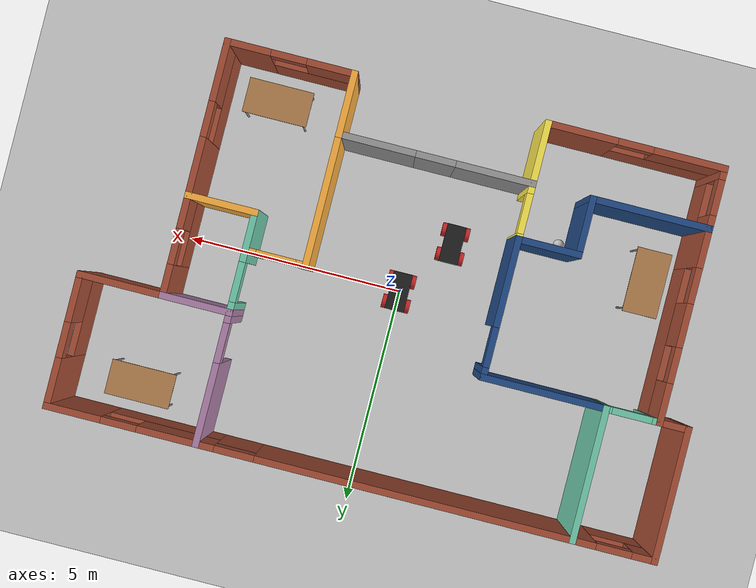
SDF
<sdf version="1.6">
 <world name="default">
  <plugin name="hello" filename="libwelcome_message.so"/>
  <light name="sun" type="directional">
   <pose>0 0 10 0 -0 0</pose>
   <diffuse>0.8 0.8 0.8 1</diffuse>
   <specular>0.2 0.2 0.2 1</specular>
   <attenuation>
    <range>1000</range>
    <constant>0.9</constant>
    <linear>0.01</linear>
    <quadratic>0.001</quadratic>
   </attenuation>
   <direction>-0.5 0.1 -0.9</direction>
  </light>
  <model name="ground_plane">
   <static>1</static>
   <link name="link">
    <collision name="collision">
     <geometry><plane><normal>0 0 1</normal><size>100 100</size></plane></geometry>
     <surface>
      <contact><collide_bitmask>65535</collide_bitmask></contact>
      <friction><ode><mu>100</mu><mu2>50</mu2></ode></friction>
     </surface>
    </collision>
    <visual name="visual">
     <cast_shadows>0</cast_shadows>
     <geometry><plane><normal>0 0 1</normal><size>100 100</size></plane></geometry>
     <material>
      <script><uri>file://media/materials/scripts/gazebo.material</uri><name>Gazebo/Grey</name></script>
     </material>
    </visual>
   </link>
  </model>
  <gravity>0 0 -9.8</gravity>
  <magnetic_field>6e-06 2.3e-05 -4.2e-05</magnetic_field>
  <atmosphere type="adiabatic"/>
  <physics name="default_physics" default="0" type="ode">
   <max_step_size>0.001</max_step_size>
   <real_time_factor>1</real_time_factor>
   <real_time_update_rate>1000</real_time_update_rate>
  </physics>
  <scene><ambient>0.4 0.4 0.4 1</ambient><background>0.7 0.7 0.7 1</background><shadows>1</shadows></scene>
  <audio><device>default</device></audio>
  <spherical_coordinates>
   <surface_model>EARTH_WGS84</surface_model>
   <latitude_deg>0</latitude_deg>
   <longitude_deg>0</longitude_deg>
   <elevation>0</elevation>
   <heading_deg>0</heading_deg>
  </spherical_coordinates>
  <model name="Building">
   <link name="Wall_103">
    <collision name="Wall_103_Collision">
     <geometry><box><size>3.1 0.15 2.5</size></box></geometry>
     <pose>0 0 1.25 0 -0 0</pose>
    </collision>
    <visual name="Wall_103_Visual">
     <pose>0 0 1.25 0 -0 0</pose>
     <geometry><box><size>3.1 0.15 2.5</size></box></geometry>
     <material>
      <script><uri>file://media/materials/scripts/gazebo.material</uri><name>Gazebo/Grey</name></script>
      <ambient>0.435294 0.796078 0.67451 1</ambient>
     </material>
     <meta><layer>0</layer></meta>
    </visual>
    <pose>-4.985 2.85 0 0 -0 1.5708</pose>
   </link>
   <link name="Wall_110">
    <pose>-2.225 -0.174996 0 0 -0 1.5708</pose>
    <visual name="Wall_110_Visual_0">
     <pose>-0.600862 0 1.25 0 -0 0</pose>
     <geometry><box><size>2.04828 0.15 2.5</size></box></geometry>
     <material>
      <script><uri>file://media/materials/scripts/gazebo.material</uri><name>Gazebo/Grey</name></script>
      <ambient>0.12549 0.290196 0.529412 1</ambient>
     </material>
     <meta><layer>0</layer></meta>
    </visual>
    <collision name="Wall_110_Collision_0">
     <geometry><box><size>2.04828 0.15 2.5</size></box></geometry>
     <pose>-0.600862 0 1.25 0 -0 0</pose>
    </collision>
    <visual name="Wall_110_Visual_1">
     <pose>1.47414 0 1.25 0 -0 0</pose>
     <geometry><box><size>0.301723 0.15 2.5</size></box></geometry>
     <material>
      <script><uri>file://media/materials/scripts/gazebo.material</uri><name>Gazebo/Grey</name></script>
      <ambient>0.12549 0.290196 0.529412 1</ambient>
     </material>
     <meta><layer>0</layer></meta>
    </visual>
    <collision name="Wall_110_Collision_1">
     <geometry><box><size>0.301723 0.15 2.5</size></box></geometry>
     <pose>1.47414 0 1.25 0 -0 0</pose>
    </collision>
    <visual name="Wall_110_Visual_2">
     <pose>0.873277 0 2.25 0 -0 0</pose>
     <geometry><box><size>0.9 0.15 0.5</size></box></geometry>
     <material>
      <script><uri>file://media/materials/scripts/gazebo.material</uri><name>Gazebo/Grey</name></script>
      <ambient>0.12549 0.290196 0.529412 1</ambient>
     </material>
     <meta><layer>0</layer></meta>
    </visual>
    <collision name="Wall_110_Collision_2">
     <geometry><box><size>0.9 0.15 0.5</size></box></geometry>
     <pose>0.873277 0 2.25 0 -0 0</pose>
    </collision>
   </link>
   <link name="Wall_112">
    <collision name="Wall_112_Collision">
     <geometry><box><size>2.91 0.15 2.5</size></box></geometry>
     <pose>0 0 1.25 0 -0 0</pose>
    </collision>
    <visual name="Wall_112_Visual">
     <pose>0 0 1.25 0 -0 0</pose>
     <geometry><box><size>2.91 0.15 2.5</size></box></geometry>
     <material>
      <script><uri>file://media/materials/scripts/gazebo.material</uri><name>Gazebo/Grey</name></script>
      <ambient>0.12549 0.290196 0.529412 1</ambient>
     </material>
     <meta><layer>0</layer></meta>
    </visual>
    <pose>-3.605 1.375 0 0 -0 3.14159</pose>
   </link>
   <link name="Wall_115">
    <pose>-2.225 -2.35 0 0 -0 1.5708</pose>
    <visual name="Wall_115_Visual_0">
     <pose>-0.551181 0 1.25 0 -0 0</pose>
     <geometry><box><size>0.297638 0.15 2.5</size></box></geometry>
     <material>
      <script><uri>file://media/materials/scripts/gazebo.material</uri><name>Gazebo/Grey</name></script>
      <ambient>0.988235 0.913725 0.309804 1</ambient>
     </material>
     <meta><layer>0</layer></meta>
    </visual>
    <collision name="Wall_115_Collision_0">
     <geometry><box><size>0.297638 0.15 2.5</size></box></geometry>
     <pose>-0.551181 0 1.25 0 -0 0</pose>
    </collision>
    <visual name="Wall_115_Visual_1">
     <pose>0.598819 0 1.25 0 -0 0</pose>
     <geometry><box><size>0.202362 0.15 2.5</size></box></geometry>
     <material>
      <script><uri>file://media/materials/scripts/gazebo.material</uri><name>Gazebo/Grey</name></script>
      <ambient>0.988235 0.913725 0.309804 1</ambient>
     </material>
     <meta><layer>0</layer></meta>
    </visual>
    <collision name="Wall_115_Collision_1">
     <geometry><box><size>0.202362 0.15 2.5</size></box></geometry>
     <pose>0.598819 0 1.25 0 -0 0</pose>
    </collision>
    <visual name="Wall_115_Visual_2">
     <pose>0.047638 0 2.25 0 -0 0</pose>
     <geometry><box><size>0.9 0.15 0.5</size></box></geometry>
     <material>
      <script><uri>file://media/materials/scripts/gazebo.material</uri><name>Gazebo/Grey</name></script>
      <ambient>0.988235 0.913725 0.309804 1</ambient>
     </material>
     <meta><layer>0</layer></meta>
    </visual>
    <collision name="Wall_115_Collision_2">
     <geometry><box><size>0.9 0.15 0.5</size></box></geometry>
     <pose>0.047638 0 2.25 0 -0 0</pose>
    </collision>
   </link>
   <link name="Wall_116">
    <collision name="Wall_116_Collision">
     <geometry><box><size>1.5 0.15 2.5</size></box></geometry>
     <pose>0 0 1.25 0 -0 0</pose>
    </collision>
    <visual name="Wall_116_Visual">
     <pose>0 0 1.25 0 -0 0</pose>
     <geometry><box><size>1.5 0.15 2.5</size></box></geometry>
     <material>
      <script><uri>file://media/materials/scripts/gazebo.material</uri><name>Gazebo/Grey</name></script>
      <ambient>0.12549 0.290196 0.529412 1</ambient>
     </material>
     <meta><layer>0</layer></meta>
    </visual>
    <pose>-2.9 -1.725 0 0 -0 3.14159</pose>
   </link>
   <link name="Wall_12">
    <pose>3.475 2.85 0 0 -0 1.5708</pose>
    <visual name="Wall_12_Visual_0">
     <pose>-1.3963 0 1.25 0 -0 0</pose>
     <geometry><box><size>0.307393 0.15 2.5</size></box></geometry>
     <material>
      <script><uri>file://media/materials/scripts/gazebo.material</uri><name>Gazebo/Grey</name></script>
      <ambient>0.678431 0.498039 0.658824 1</ambient>
     </material>
     <meta><layer>0</layer></meta>
    </visual>
    <collision name="Wall_12_Collision_0">
     <geometry><box><size>0.307393 0.15 2.5</size></box></geometry>
     <pose>-1.3963 0 1.25 0 -0 0</pose>
    </collision>
    <visual name="Wall_12_Visual_1">
     <pose>0.603697 0 1.25 0 -0 0</pose>
     <geometry><box><size>1.89261 0.15 2.5</size></box></geometry>
     <material>
      <script><uri>file://media/materials/scripts/gazebo.material</uri><name>Gazebo/Grey</name></script>
      <ambient>0.678431 0.498039 0.658824 1</ambient>
     </material>
     <meta><layer>0</layer></meta>
    </visual>
    <collision name="Wall_12_Collision_1">
     <geometry><box><size>1.89261 0.15 2.5</size></box></geometry>
     <pose>0.603697 0 1.25 0 -0 0</pose>
    </collision>
    <visual name="Wall_12_Visual_2">
     <pose>-0.792607 0 2.25 0 -0 0</pose>
     <geometry><box><size>0.9 0.15 0.5</size></box></geometry>
     <material>
      <script><uri>file://media/materials/scripts/gazebo.material</uri><name>Gazebo/Grey</name></script>
      <ambient>0.678431 0.498039 0.658824 1</ambient>
     </material>
     <meta><layer>0</layer></meta>
    </visual>
    <collision name="Wall_12_Collision_2">
     <geometry><box><size>0.9 0.15 0.5</size></box></geometry>
     <pose>-0.792607 0 2.25 0 -0 0</pose>
    </collision>
   </link>
   <link name="Wall_121">
    <collision name="Wall_121_Collision">
     <geometry><box><size>1.4 0.15 2.5</size></box></geometry>
     <pose>0 0 1.25 0 -0 0</pose>
    </collision>
    <visual name="Wall_121_Visual">
     <pose>0 0 1.25 0 -0 0</pose>
     <geometry><box><size>1.4 0.15 2.5</size></box></geometry>
     <material>
      <script><uri>file://media/materials/scripts/gazebo.material</uri><name>Gazebo/Grey</name></script>
      <ambient>0.12549 0.290196 0.529412 1</ambient>
     </material>
     <meta><layer>0</layer></meta>
    </visual>
    <pose>-3.575 -2.35 0 0 -0 -1.5708</pose>
   </link>
   <link name="Wall_123">
    <collision name="Wall_123_Collision">
     <geometry><box><size>2.76 0.15 2.5</size></box></geometry>
     <pose>0 0 1.25 0 -0 0</pose>
    </collision>
    <visual name="Wall_123_Visual">
     <pose>0 0 1.25 0 -0 0</pose>
     <geometry><box><size>2.76 0.15 2.5</size></box></geometry>
     <material>
      <script><uri>file://media/materials/scripts/gazebo.material</uri><name>Gazebo/Grey</name></script>
      <ambient>0.12549 0.290196 0.529412 1</ambient>
     </material>
     <meta><layer>0</layer></meta>
    </visual>
    <pose>-4.88 -2.97499 0 0 -0 3.14159</pose>
   </link>
   <link name="Wall_125">
    <pose>-6.185 -3.65 0 0 -0 1.5708</pose>
    <visual name="Wall_125_Visual_0">
     <pose>-0.587283 0 1.25 0 -0 0</pose>
     <geometry><box><size>0.325434 0.15 2.5</size></box></geometry>
     <material>
      <script><uri>file://media/materials/scripts/gazebo.material</uri><name>Gazebo/Bricks</name></script>
      <ambient>1 1 1 1</ambient>
     </material>
     <meta><layer>0</layer></meta>
    </visual>
    <collision name="Wall_125_Collision_0">
     <geometry><box><size>0.325434 0.15 2.5</size></box></geometry>
     <pose>-0.587283 0 1.25 0 -0 0</pose>
    </collision>
    <visual name="Wall_125_Visual_1">
     <pose>0.162717 0 0.65 0 -0 0</pose>
     <geometry><box><size>1.17457 0.15 1.3</size></box></geometry>
     <material>
      <script><uri>file://media/materials/scripts/gazebo.material</uri><name>Gazebo/Bricks</name></script>
      <ambient>1 1 1 1</ambient>
     </material>
     <meta><layer>0</layer></meta>
    </visual>
    <collision name="Wall_125_Collision_1">
     <geometry><box><size>1.17457 0.15 1.3</size></box></geometry>
     <pose>0.162717 0 0.65 0 -0 0</pose>
    </collision>
    <visual name="Wall_125_Visual_2">
     <pose>0.562717 0 1.9 0 -0 0</pose>
     <geometry><box><size>0.374566 0.15 1.2</size></box></geometry>
     <material>
      <script><uri>file://media/materials/scripts/gazebo.material</uri><name>Gazebo/Bricks</name></script>
      <ambient>1 1 1 1</ambient>
     </material>
     <meta><layer>0</layer></meta>
    </visual>
    <collision name="Wall_125_Collision_2">
     <geometry><box><size>0.374566 0.15 1.2</size></box></geometry>
     <pose>0.562717 0 1.9 0 -0 0</pose>
    </collision>
    <visual name="Wall_125_Visual_3">
     <pose>-0.024566 0 2.3 0 -0 0</pose>
     <geometry><box><size>0.8 0.15 0.4</size></box></geometry>
     <material>
      <script><uri>file://media/materials/scripts/gazebo.material</uri><name>Gazebo/Bricks</name></script>
      <ambient>1 1 1 1</ambient>
     </material>
     <meta><layer>0</layer></meta>
    </visual>
    <collision name="Wall_125_Collision_3">
     <geometry><box><size>0.8 0.15 0.4</size></box></geometry>
     <pose>-0.024566 0 2.3 0 -0 0</pose>
    </collision>
   </link>
   <link name="Wall_128">
    <pose>-6.185 -0.799996 0 0 -0 1.5708</pose>
    <visual name="Wall_128_Visual_0">
     <pose>-1.77232 0 1.25 0 -0 0</pose>
     <geometry><box><size>0.955364 0.15 2.5</size></box></geometry>
     <material>
      <script><uri>file://media/materials/scripts/gazebo.material</uri><name>Gazebo/Bricks</name></script>
      <ambient>1 1 1 1</ambient>
     </material>
     <meta><layer>0</layer></meta>
    </visual>
    <collision name="Wall_128_Collision_0">
     <geometry><box><size>0.955364 0.15 2.5</size></box></geometry>
     <pose>-1.77232 0 1.25 0 -0 0</pose>
    </collision>
    <visual name="Wall_128_Visual_1">
     <pose>0.477682 0 0.65 0 -0 0</pose>
     <geometry><box><size>3.54464 0.15 1.3</size></box></geometry>
     <material>
      <script><uri>file://media/materials/scripts/gazebo.material</uri><name>Gazebo/Bricks</name></script>
      <ambient>1 1 1 1</ambient>
     </material>
     <meta><layer>0</layer></meta>
    </visual>
    <collision name="Wall_128_Collision_1">
     <geometry><box><size>3.54464 0.15 1.3</size></box></geometry>
     <pose>0.477682 0 0.65 0 -0 0</pose>
    </collision>
    <visual name="Wall_128_Visual_2">
     <pose>-0.000839 0 1.9 0 -0 0</pose>
     <geometry><box><size>0.987594 0.15 1.2</size></box></geometry>
     <material>
      <script><uri>file://media/materials/scripts/gazebo.material</uri><name>Gazebo/Bricks</name></script>
      <ambient>1 1 1 1</ambient>
     </material>
     <meta><layer>0</layer></meta>
    </visual>
    <collision name="Wall_128_Collision_2">
     <geometry><box><size>0.987594 0.15 1.2</size></box></geometry>
     <pose>-0.000839 0 1.9 0 -0 0</pose>
    </collision>
    <visual name="Wall_128_Visual_3">
     <pose>1.77148 0 1.9 0 -0 0</pose>
     <geometry><box><size>0.957042 0.15 1.2</size></box></geometry>
     <material>
      <script><uri>file://media/materials/scripts/gazebo.material</uri><name>Gazebo/Bricks</name></script>
      <ambient>1 1 1 1</ambient>
     </material>
     <meta><layer>0</layer></meta>
    </visual>
    <collision name="Wall_128_Collision_3">
     <geometry><box><size>0.957042 0.15 1.2</size></box></geometry>
     <pose>1.77148 0 1.9 0 -0 0</pose>
    </collision>
    <visual name="Wall_128_Visual_4">
     <pose>-0.894636 0 2.3 0 -0 0</pose>
     <geometry><box><size>0.8 0.15 0.4</size></box></geometry>
     <material>
      <script><uri>file://media/materials/scripts/gazebo.material</uri><name>Gazebo/Bricks</name></script>
      <ambient>1 1 1 1</ambient>
     </material>
     <meta><layer>0</layer></meta>
    </visual>
    <collision name="Wall_128_Collision_4">
     <geometry><box><size>0.8 0.15 0.4</size></box></geometry>
     <pose>-0.894636 0 2.3 0 -0 0</pose>
    </collision>
    <visual name="Wall_128_Visual_5">
     <pose>0.892958 0 2.3 0 -0 0</pose>
     <geometry><box><size>0.8 0.15 0.4</size></box></geometry>
     <material>
      <script><uri>file://media/materials/scripts/gazebo.material</uri><name>Gazebo/Bricks</name></script>
      <ambient>1 1 1 1</ambient>
     </material>
     <meta><layer>0</layer></meta>
    </visual>
    <collision name="Wall_128_Collision_5">
     <geometry><box><size>0.8 0.15 0.4</size></box></geometry>
     <pose>0.892958 0 2.3 0 -0 0</pose>
    </collision>
   </link>
   <link name="Wall_130">
    <collision name="Wall_130_Collision">
     <geometry><box><size>1.65 0.15 2.5</size></box></geometry>
     <pose>0 0 1.25 0 -0 0</pose>
    </collision>
    <visual name="Wall_130_Visual">
     <pose>0 0 1.25 0 -0 0</pose>
     <geometry><box><size>1.65 0.15 2.5</size></box></geometry>
     <material>
      <script><uri>file://media/materials/scripts/gazebo.material</uri><name>Gazebo/Grey</name></script>
      <ambient>0.678431 0.498039 0.658824 1</ambient>
     </material>
     <meta><layer>0</layer></meta>
    </visual>
    <pose>4.225 1.375 0 0 -0 3.14159</pose>
   </link>
   <link name="Wall_132">
    <collision name="Wall_132_Collision">
     <geometry><box><size>1.5 0.15 2.5</size></box></geometry>
     <pose>0 0 1.25 0 -0 0</pose>
    </collision>
    <visual name="Wall_132_Visual">
     <pose>0 0 1.25 0 -0 0</pose>
     <geometry><box><size>1.5 0.15 2.5</size></box></geometry>
     <material>
      <script><uri>file://media/materials/scripts/gazebo.material</uri><name>Gazebo/Grey</name></script>
      <ambient>0.988235 0.686275 0.243137 1</ambient>
     </material>
     <meta><layer>0</layer></meta>
    </visual>
    <pose>2.125 -3.65 0 0 -0 1.5708</pose>
   </link>
   <link name="Wall_133">
    <collision name="Wall_133_Collision">
     <geometry><box><size>3.1 0.15 2.5</size></box></geometry>
     <pose>0 0 1.25 0 -0 0</pose>
    </collision>
    <visual name="Wall_133_Visual">
     <pose>0 0 1.25 0 -0 0</pose>
     <geometry><box><size>3.1 0.15 2.5</size></box></geometry>
     <material>
      <script><uri>file://media/materials/scripts/gazebo.material</uri><name>Gazebo/Grey</name></script>
      <ambient>0.988235 0.686275 0.243137 1</ambient>
     </material>
     <meta><layer>0</layer></meta>
    </visual>
    <pose>2.125 -1.5 0 0 -0 1.5708</pose>
   </link>
   <link name="Wall_137">
    <collision name="Wall_137_Collision">
     <geometry><box><size>0.79 0.15 2.5</size></box></geometry>
     <pose>0 0 1.25 0 -0 0</pose>
    </collision>
    <visual name="Wall_137_Visual">
     <pose>0 0 1.25 0 -0 0</pose>
     <geometry><box><size>0.79 0.15 2.5</size></box></geometry>
     <material>
      <script><uri>file://media/materials/scripts/gazebo.material</uri><name>Gazebo/Bricks</name></script>
      <ambient>1 1 1 1</ambient>
     </material>
     <meta><layer>0</layer></meta>
    </visual>
    <pose>-6.505 1.375 0 0 -0 0</pose>
   </link>
   <link name="Wall_138">
    <pose>-5.585 1.375 0 0 -0 0</pose>
    <visual name="Wall_138_Visual_0">
     <pose>-0.55259 0 1.25 0 -0 0</pose>
     <geometry><box><size>0.244819 0.15 2.5</size></box></geometry>
     <material>
      <script><uri>file://media/materials/scripts/gazebo.material</uri><name>Gazebo/Grey</name></script>
      <ambient>0.435294 0.796078 0.67451 1</ambient>
     </material>
     <meta><layer>0</layer></meta>
    </visual>
    <collision name="Wall_138_Collision_0">
     <geometry><box><size>0.244819 0.15 2.5</size></box></geometry>
     <pose>-0.55259 0 1.25 0 -0 0</pose>
    </collision>
    <visual name="Wall_138_Visual_1">
     <pose>0.57241 0 1.25 0 -0 0</pose>
     <geometry><box><size>0.205181 0.15 2.5</size></box></geometry>
     <material>
      <script><uri>file://media/materials/scripts/gazebo.material</uri><name>Gazebo/Grey</name></script>
      <ambient>0.435294 0.796078 0.67451 1</ambient>
     </material>
     <meta><layer>0</layer></meta>
    </visual>
    <collision name="Wall_138_Collision_1">
     <geometry><box><size>0.205181 0.15 2.5</size></box></geometry>
     <pose>0.57241 0 1.25 0 -0 0</pose>
    </collision>
    <visual name="Wall_138_Visual_2">
     <pose>0.019819 0 2.25 0 -0 0</pose>
     <geometry><box><size>0.9 0.15 0.5</size></box></geometry>
     <material>
      <script><uri>file://media/materials/scripts/gazebo.material</uri><name>Gazebo/Grey</name></script>
      <ambient>0.435294 0.796078 0.67451 1</ambient>
     </material>
     <meta><layer>0</layer></meta>
    </visual>
    <collision name="Wall_138_Collision_2">
     <geometry><box><size>0.9 0.15 0.5</size></box></geometry>
     <pose>0.019819 0 2.25 0 -0 0</pose>
    </collision>
   </link>
   <link name="Wall_22">
    <pose>3.475 0.250004 0 0 -0 -1.5708</pose>
    <visual name="Wall_22_Visual_0">
     <pose>-1.0443 0 1.25 0 -0 0</pose>
     <geometry><box><size>0.311394 0.15 2.5</size></box></geometry>
     <material>
      <script><uri>file://media/materials/scripts/gazebo.material</uri><name>Gazebo/Grey</name></script>
      <ambient>0.435294 0.796078 0.67451 1</ambient>
     </material>
     <meta><layer>0</layer></meta>
    </visual>
    <collision name="Wall_22_Collision_0">
     <geometry><box><size>0.311394 0.15 2.5</size></box></geometry>
     <pose>-1.0443 0 1.25 0 -0 0</pose>
    </collision>
    <visual name="Wall_22_Visual_1">
     <pose>0.605697 0 1.25 0 -0 0</pose>
     <geometry><box><size>1.18861 0.15 2.5</size></box></geometry>
     <material>
      <script><uri>file://media/materials/scripts/gazebo.material</uri><name>Gazebo/Grey</name></script>
      <ambient>0.435294 0.796078 0.67451 1</ambient>
     </material>
     <meta><layer>0</layer></meta>
    </visual>
    <collision name="Wall_22_Collision_1">
     <geometry><box><size>1.18861 0.15 2.5</size></box></geometry>
     <pose>0.605697 0 1.25 0 -0 0</pose>
    </collision>
    <visual name="Wall_22_Visual_2">
     <pose>-0.438606 0 2.25 0 -0 0</pose>
     <geometry><box><size>0.9 0.15 0.5</size></box></geometry>
     <material>
      <script><uri>file://media/materials/scripts/gazebo.material</uri><name>Gazebo/Grey</name></script>
      <ambient>0.435294 0.796078 0.67451 1</ambient>
     </material>
     <meta><layer>0</layer></meta>
    </visual>
    <collision name="Wall_22_Collision_2">
     <geometry><box><size>0.9 0.15 0.5</size></box></geometry>
     <pose>-0.438606 0 2.25 0 -0 0</pose>
    </collision>
   </link>
   <link name="Wall_27">
    <collision name="Wall_27_Collision">
     <geometry><box><size>2 0.15 2.5</size></box></geometry>
     <pose>0 0 1.25 0 -0 0</pose>
    </collision>
    <visual name="Wall_27_Visual">
     <pose>0 0 1.25 0 -0 0</pose>
     <geometry><box><size>2 0.15 2.5</size></box></geometry>
     <material>
      <script><uri>file://media/materials/scripts/gazebo.material</uri><name>Gazebo/Bricks</name></script>
      <ambient>1 1 1 1</ambient>
     </material>
     <meta><layer>0</layer></meta>
    </visual>
    <pose>5.9 1.375 0 0 -0 3.14159</pose>
   </link>
   <link name="Wall_28">
    <pose>4.975 0.250004 0 0 -0 -1.5708</pose>
    <visual name="Wall_28_Visual_0">
     <pose>-0.81199 0 1.25 0 -0 0</pose>
     <geometry><box><size>0.77602 0.15 2.5</size></box></geometry>
     <material>
      <script><uri>file://media/materials/scripts/gazebo.material</uri><name>Gazebo/Bricks</name></script>
      <ambient>1 1 1 1</ambient>
     </material>
     <meta><layer>0</layer></meta>
    </visual>
    <collision name="Wall_28_Collision_0">
     <geometry><box><size>0.77602 0.15 2.5</size></box></geometry>
     <pose>-0.81199 0 1.25 0 -0 0</pose>
    </collision>
    <visual name="Wall_28_Visual_1">
     <pose>0.38801 0 0.65 0 -0 0</pose>
     <geometry><box><size>1.62398 0.15 1.3</size></box></geometry>
     <material>
      <script><uri>file://media/materials/scripts/gazebo.material</uri><name>Gazebo/Bricks</name></script>
      <ambient>1 1 1 1</ambient>
     </material>
     <meta><layer>0</layer></meta>
    </visual>
    <collision name="Wall_28_Collision_1">
     <geometry><box><size>1.62398 0.15 1.3</size></box></geometry>
     <pose>0.38801 0 0.65 0 -0 0</pose>
    </collision>
    <visual name="Wall_28_Visual_2">
     <pose>0.78801 0 1.9 0 -0 0</pose>
     <geometry><box><size>0.82398 0.15 1.2</size></box></geometry>
     <material>
      <script><uri>file://media/materials/scripts/gazebo.material</uri><name>Gazebo/Bricks</name></script>
      <ambient>1 1 1 1</ambient>
     </material>
     <meta><layer>0</layer></meta>
    </visual>
    <collision name="Wall_28_Collision_2">
     <geometry><box><size>0.82398 0.15 1.2</size></box></geometry>
     <pose>0.78801 0 1.9 0 -0 0</pose>
    </collision>
    <visual name="Wall_28_Visual_3">
     <pose>-0.02398 0 2.3 0 -0 0</pose>
     <geometry><box><size>0.8 0.15 0.4</size></box></geometry>
     <material>
      <script><uri>file://media/materials/scripts/gazebo.material</uri><name>Gazebo/Bricks</name></script>
      <ambient>1 1 1 1</ambient>
     </material>
     <meta><layer>0</layer></meta>
    </visual>
    <collision name="Wall_28_Collision_3">
     <geometry><box><size>0.8 0.15 0.4</size></box></geometry>
     <pose>-0.02398 0 2.3 0 -0 0</pose>
    </collision>
   </link>
   <link name="Wall_31">
    <collision name="Wall_31_Collision">
     <geometry><box><size>1.65 0.15 2.5</size></box></geometry>
     <pose>0 0 1.25 0 -0 0</pose>
    </collision>
    <visual name="Wall_31_Visual">
     <pose>0 0 1.25 0 -0 0</pose>
     <geometry><box><size>1.65 0.15 2.5</size></box></geometry>
     <material>
      <script><uri>file://media/materials/scripts/gazebo.material</uri><name>Gazebo/Grey</name></script>
      <ambient>0.988235 0.686275 0.243137 1</ambient>
     </material>
     <meta><layer>0</layer></meta>
    </visual>
    <pose>4.225 -0.874996 0 0 -0 0</pose>
   </link>
   <link name="Wall_33">
    <pose>4.975 -2.59999 0 0 -0 -1.5708</pose>
    <visual name="Wall_33_Visual_0">
     <pose>-1.10578 0 1.25 0 -0 0</pose>
     <geometry><box><size>1.38843 0.15 2.5</size></box></geometry>
     <material>
      <script><uri>file://media/materials/scripts/gazebo.material</uri><name>Gazebo/Bricks</name></script>
      <ambient>1 1 1 1</ambient>
     </material>
     <meta><layer>0</layer></meta>
    </visual>
    <collision name="Wall_33_Collision_0">
     <geometry><box><size>1.38843 0.15 2.5</size></box></geometry>
     <pose>-1.10578 0 1.25 0 -0 0</pose>
    </collision>
    <visual name="Wall_33_Visual_1">
     <pose>0.694217 0 0.65 0 -0 0</pose>
     <geometry><box><size>2.21157 0.15 1.3</size></box></geometry>
     <material>
      <script><uri>file://media/materials/scripts/gazebo.material</uri><name>Gazebo/Bricks</name></script>
      <ambient>1 1 1 1</ambient>
     </material>
     <meta><layer>0</layer></meta>
    </visual>
    <collision name="Wall_33_Collision_1">
     <geometry><box><size>2.21157 0.15 1.3</size></box></geometry>
     <pose>0.694217 0 0.65 0 -0 0</pose>
    </collision>
    <visual name="Wall_33_Visual_2">
     <pose>1.09422 0 1.9 0 -0 0</pose>
     <geometry><box><size>1.41157 0.15 1.2</size></box></geometry>
     <material>
      <script><uri>file://media/materials/scripts/gazebo.material</uri><name>Gazebo/Bricks</name></script>
      <ambient>1 1 1 1</ambient>
     </material>
     <meta><layer>0</layer></meta>
    </visual>
    <collision name="Wall_33_Collision_2">
     <geometry><box><size>1.41157 0.15 1.2</size></box></geometry>
     <pose>1.09422 0 1.9 0 -0 0</pose>
    </collision>
    <visual name="Wall_33_Visual_3">
     <pose>-0.011567 0 2.3 0 -0 0</pose>
     <geometry><box><size>0.8 0.15 0.4</size></box></geometry>
     <material>
      <script><uri>file://media/materials/scripts/gazebo.material</uri><name>Gazebo/Bricks</name></script>
      <ambient>1 1 1 1</ambient>
     </material>
     <meta><layer>0</layer></meta>
    </visual>
    <collision name="Wall_33_Collision_3">
     <geometry><box><size>0.8 0.15 0.4</size></box></geometry>
     <pose>-0.011567 0 2.3 0 -0 0</pose>
    </collision>
   </link>
   <link name="Wall_4">
    <pose>-0 4.325 0 0 -0 3.14159</pose>
    <visual name="Wall_4_Visual_0">
     <pose>-6.2573 0 1.25 0 -0 0</pose>
     <geometry><box><size>1.2854 0.15 2.5</size></box></geometry>
     <material>
      <script><uri>file://media/materials/scripts/gazebo.material</uri><name>Gazebo/Bricks</name></script>
      <ambient>1 1 1 1</ambient>
     </material>
     <meta><layer>0</layer></meta>
    </visual>
    <collision name="Wall_4_Collision_0">
     <geometry><box><size>1.2854 0.15 2.5</size></box></geometry>
     <pose>-6.2573 0 1.25 0 -0 0</pose>
    </collision>
    <visual name="Wall_4_Visual_1">
     <pose>1.66661 0 1.25 0 -0 0</pose>
     <geometry><box><size>7.68067 0.15 2.5</size></box></geometry>
     <material>
      <script><uri>file://media/materials/scripts/gazebo.material</uri><name>Gazebo/Bricks</name></script>
      <ambient>1 1 1 1</ambient>
     </material>
     <meta><layer>0</layer></meta>
    </visual>
    <collision name="Wall_4_Collision_1">
     <geometry><box><size>7.68067 0.15 2.5</size></box></geometry>
     <pose>1.66661 0 1.25 0 -0 0</pose>
    </collision>
    <visual name="Wall_4_Visual_2">
     <pose>-4.34416 0 0.65 0 -0 0</pose>
     <geometry><box><size>2.54088 0.15 1.3</size></box></geometry>
     <material>
      <script><uri>file://media/materials/scripts/gazebo.material</uri><name>Gazebo/Bricks</name></script>
      <ambient>1 1 1 1</ambient>
     </material>
     <meta><layer>0</layer></meta>
    </visual>
    <collision name="Wall_4_Collision_2">
     <geometry><box><size>2.54088 0.15 1.3</size></box></geometry>
     <pose>-4.34416 0 0.65 0 -0 0</pose>
    </collision>
    <visual name="Wall_4_Visual_3">
     <pose>6.20347 0 0.65 0 -0 0</pose>
     <geometry><box><size>1.39305 0.15 1.3</size></box></geometry>
     <material>
      <script><uri>file://media/materials/scripts/gazebo.material</uri><name>Gazebo/Bricks</name></script>
      <ambient>1 1 1 1</ambient>
     </material>
     <meta><layer>0</layer></meta>
    </visual>
    <collision name="Wall_4_Collision_3">
     <geometry><box><size>1.39305 0.15 1.3</size></box></geometry>
     <pose>6.20347 0 0.65 0 -0 0</pose>
    </collision>
    <visual name="Wall_4_Visual_4">
     <pose>-3.94416 0 1.9 0 -0 0</pose>
     <geometry><box><size>1.74088 0.15 1.2</size></box></geometry>
     <material>
      <script><uri>file://media/materials/scripts/gazebo.material</uri><name>Gazebo/Bricks</name></script>
      <ambient>1 1 1 1</ambient>
     </material>
     <meta><layer>0</layer></meta>
    </visual>
    <collision name="Wall_4_Collision_4">
     <geometry><box><size>1.74088 0.15 1.2</size></box></geometry>
     <pose>-3.94416 0 1.9 0 -0 0</pose>
    </collision>
    <visual name="Wall_4_Visual_5">
     <pose>-3.94416 0 1.9 0 -0 0</pose>
     <geometry><box><size>1.74088 0.15 1.2</size></box></geometry>
     <material>
      <script><uri>file://media/materials/scripts/gazebo.material</uri><name>Gazebo/Bricks</name></script>
      <ambient>1 1 1 1</ambient>
     </material>
     <meta><layer>0</layer></meta>
    </visual>
    <collision name="Wall_4_Collision_5">
     <geometry><box><size>1.74088 0.15 1.2</size></box></geometry>
     <pose>-3.94416 0 1.9 0 -0 0</pose>
    </collision>
    <visual name="Wall_4_Visual_6">
     <pose>6.60347 0 1.9 0 -0 0</pose>
     <geometry><box><size>0.593052 0.15 1.2</size></box></geometry>
     <material>
      <script><uri>file://media/materials/scripts/gazebo.material</uri><name>Gazebo/Bricks</name></script>
      <ambient>1 1 1 1</ambient>
     </material>
     <meta><layer>0</layer></meta>
    </visual>
    <collision name="Wall_4_Collision_6">
     <geometry><box><size>0.593052 0.15 1.2</size></box></geometry>
     <pose>6.60347 0 1.9 0 -0 0</pose>
    </collision>
    <visual name="Wall_4_Visual_7">
     <pose>-2.62372 0 2.25 0 -0 0</pose>
     <geometry><box><size>0.9 0.15 0.5</size></box></geometry>
     <material>
      <script><uri>file://media/materials/scripts/gazebo.material</uri><name>Gazebo/Bricks</name></script>
      <ambient>1 1 1 1</ambient>
     </material>
     <meta><layer>0</layer></meta>
    </visual>
    <collision name="Wall_4_Collision_7">
     <geometry><box><size>0.9 0.15 0.5</size></box></geometry>
     <pose>-2.62372 0 2.25 0 -0 0</pose>
    </collision>
    <visual name="Wall_4_Visual_8">
     <pose>-2.62372 0 1.25 0 -0 0</pose>
     <geometry><box><size>0.9 0.15 2.5</size></box></geometry>
     <material>
      <script><uri>file://media/materials/scripts/gazebo.material</uri><name>Gazebo/Bricks</name></script>
      <ambient>1 1 1 1</ambient>
     </material>
     <meta><layer>0</layer></meta>
    </visual>
    <collision name="Wall_4_Collision_8">
     <geometry><box><size>0.9 0.15 2.5</size></box></geometry>
     <pose>-2.62372 0 1.25 0 -0 0</pose>
    </collision>
    <visual name="Wall_4_Visual_9">
     <pose>-5.2146 0 2.3 0 -0 0</pose>
     <geometry><box><size>0.8 0.15 0.4</size></box></geometry>
     <material>
      <script><uri>file://media/materials/scripts/gazebo.material</uri><name>Gazebo/Bricks</name></script>
      <ambient>1 1 1 1</ambient>
     </material>
     <meta><layer>0</layer></meta>
    </visual>
    <collision name="Wall_4_Collision_9">
     <geometry><box><size>0.8 0.15 0.4</size></box></geometry>
     <pose>-5.2146 0 2.3 0 -0 0</pose>
    </collision>
    <visual name="Wall_4_Visual_10">
     <pose>5.90695 0 2.3 0 -0 0</pose>
     <geometry><box><size>0.8 0.15 0.4</size></box></geometry>
     <material>
      <script><uri>file://media/materials/scripts/gazebo.material</uri><name>Gazebo/Bricks</name></script>
      <ambient>1 1 1 1</ambient>
     </material>
     <meta><layer>0</layer></meta>
    </visual>
    <collision name="Wall_4_Collision_10">
     <geometry><box><size>0.8 0.15 0.4</size></box></geometry>
     <pose>5.90695 0 2.3 0 -0 0</pose>
    </collision>
   </link>
   <link name="Wall_40">
    <pose>2.8 -0.024996 0 0 -0 3.14159</pose>
    <visual name="Wall_40_Visual_0">
     <pose>-0.597696 0 1.25 0 -0 0</pose>
     <geometry><box><size>0.304607 0.15 2.5</size></box></geometry>
     <material>
      <script><uri>file://media/materials/scripts/gazebo.material</uri><name>Gazebo/Grey</name></script>
      <ambient>0.988235 0.686275 0.243137 1</ambient>
     </material>
     <meta><layer>0</layer></meta>
    </visual>
    <collision name="Wall_40_Collision_0">
     <geometry><box><size>0.304607 0.15 2.5</size></box></geometry>
     <pose>-0.597696 0 1.25 0 -0 0</pose>
    </collision>
    <visual name="Wall_40_Visual_1">
     <pose>0.602304 0 1.25 0 -0 0</pose>
     <geometry><box><size>0.295393 0.15 2.5</size></box></geometry>
     <material>
      <script><uri>file://media/materials/scripts/gazebo.material</uri><name>Gazebo/Grey</name></script>
      <ambient>0.988235 0.686275 0.243137 1</ambient>
     </material>
     <meta><layer>0</layer></meta>
    </visual>
    <collision name="Wall_40_Collision_1">
     <geometry><box><size>0.295393 0.15 2.5</size></box></geometry>
     <pose>0.602304 0 1.25 0 -0 0</pose>
    </collision>
    <visual name="Wall_40_Visual_2">
     <pose>0.004607 0 2.25 0 -0 0</pose>
     <geometry><box><size>0.9 0.15 0.5</size></box></geometry>
     <material>
      <script><uri>file://media/materials/scripts/gazebo.material</uri><name>Gazebo/Grey</name></script>
      <ambient>0.988235 0.686275 0.243137 1</ambient>
     </material>
     <meta><layer>0</layer></meta>
    </visual>
    <collision name="Wall_40_Collision_2">
     <geometry><box><size>0.9 0.15 0.5</size></box></geometry>
     <pose>0.004607 0 2.25 0 -0 0</pose>
    </collision>
   </link>
   <link name="Wall_47">
    <pose>-0.05 -2.97499 0 0 -0 3.14159</pose>
    <visual name="Wall_47_Visual_0">
     <pose>-1.35045 0 1.25 0 -0 0</pose>
     <geometry><box><size>1.79909 0.15 2.5</size></box></geometry>
     <material>
      <script><uri>file://media/materials/scripts/gazebo.material</uri><name>Gazebo/Grey</name></script>
      <ambient>0.180392 0.203922 0.211765 1</ambient>
     </material>
     <meta><layer>0</layer></meta>
    </visual>
    <collision name="Wall_47_Collision_0">
     <geometry><box><size>1.79909 0.15 2.5</size></box></geometry>
     <pose>-1.35045 0 1.25 0 -0 0</pose>
    </collision>
    <visual name="Wall_47_Visual_1">
     <pose>1.34955 0 1.25 0 -0 0</pose>
     <geometry><box><size>1.80091 0.15 2.5</size></box></geometry>
     <material>
      <script><uri>file://media/materials/scripts/gazebo.material</uri><name>Gazebo/Grey</name></script>
      <ambient>0.180392 0.203922 0.211765 1</ambient>
     </material>
     <meta><layer>0</layer></meta>
    </visual>
    <collision name="Wall_47_Collision_1">
     <geometry><box><size>1.80091 0.15 2.5</size></box></geometry>
     <pose>1.34955 0 1.25 0 -0 0</pose>
    </collision>
    <visual name="Wall_47_Visual_2">
     <pose>-0.000907 0 1.25 0 -0 0</pose>
     <geometry><box><size>0.9 0.15 2.5</size></box></geometry>
     <material>
      <script><uri>file://media/materials/scripts/gazebo.material</uri><name>Gazebo/Grey</name></script>
      <ambient>0.180392 0.203922 0.211765 1</ambient>
     </material>
     <meta><layer>0</layer></meta>
    </visual>
    <collision name="Wall_47_Collision_2">
     <geometry><box><size>0.9 0.15 2.5</size></box></geometry>
     <pose>-0.000907 0 1.25 0 -0 0</pose>
    </collision>
   </link>
   <link name="Wall_48">
    <collision name="Wall_48_Collision">
     <geometry><box><size>1.50002 0.15 2.5</size></box></geometry>
     <pose>0 0 1.25 0 -0 0</pose>
    </collision>
    <visual name="Wall_48_Visual">
     <pose>0 0 1.25 0 -0 0</pose>
     <geometry><box><size>1.50002 0.15 2.5</size></box></geometry>
     <material>
      <script><uri>file://media/materials/scripts/gazebo.material</uri><name>Gazebo/Grey</name></script>
      <ambient>0.988235 0.913725 0.309804 1</ambient>
     </material>
     <meta><layer>0</layer></meta>
    </visual>
    <pose>-2.225 -3.65 0 0 -0 -1.5708</pose>
   </link>
   <link name="Wall_57">
    <pose>3.55 -4.325 0 0 -0 3.14159</pose>
    <visual name="Wall_57_Visual_0">
     <pose>-0.973357 0 1.25 0 -0 0</pose>
     <geometry><box><size>1.05329 0.15 2.5</size></box></geometry>
     <material>
      <script><uri>file://media/materials/scripts/gazebo.material</uri><name>Gazebo/Bricks</name></script>
      <ambient>1 1 1 1</ambient>
     </material>
     <meta><layer>0</layer></meta>
    </visual>
    <collision name="Wall_57_Collision_0">
     <geometry><box><size>1.05329 0.15 2.5</size></box></geometry>
     <pose>-0.973357 0 1.25 0 -0 0</pose>
    </collision>
    <visual name="Wall_57_Visual_1">
     <pose>0.526643 0 0.65 0 -0 0</pose>
     <geometry><box><size>1.94671 0.15 1.3</size></box></geometry>
     <material>
      <script><uri>file://media/materials/scripts/gazebo.material</uri><name>Gazebo/Bricks</name></script>
      <ambient>1 1 1 1</ambient>
     </material>
     <meta><layer>0</layer></meta>
    </visual>
    <collision name="Wall_57_Collision_1">
     <geometry><box><size>1.94671 0.15 1.3</size></box></geometry>
     <pose>0.526643 0 0.65 0 -0 0</pose>
    </collision>
    <visual name="Wall_57_Visual_2">
     <pose>0.926643 0 1.9 0 -0 0</pose>
     <geometry><box><size>1.14671 0.15 1.2</size></box></geometry>
     <material>
      <script><uri>file://media/materials/scripts/gazebo.material</uri><name>Gazebo/Bricks</name></script>
      <ambient>1 1 1 1</ambient>
     </material>
     <meta><layer>0</layer></meta>
    </visual>
    <collision name="Wall_57_Collision_2">
     <geometry><box><size>1.14671 0.15 1.2</size></box></geometry>
     <pose>0.926643 0 1.9 0 -0 0</pose>
    </collision>
    <visual name="Wall_57_Visual_3">
     <pose>-0.046715 0 2.3 0 -0 0</pose>
     <geometry><box><size>0.8 0.15 0.4</size></box></geometry>
     <material>
      <script><uri>file://media/materials/scripts/gazebo.material</uri><name>Gazebo/Bricks</name></script>
      <ambient>1 1 1 1</ambient>
     </material>
     <meta><layer>0</layer></meta>
    </visual>
    <collision name="Wall_57_Collision_3">
     <geometry><box><size>0.8 0.15 0.4</size></box></geometry>
     <pose>-0.046715 0 2.3 0 -0 0</pose>
    </collision>
   </link>
   <link name="Wall_61">
    <pose>-4.205 -4.325 0 0 -0 3.14159</pose>
    <visual name="Wall_61_Visual_0">
     <pose>-1.23072 0 1.25 0 -0 0</pose>
     <geometry><box><size>1.64855 0.15 2.5</size></box></geometry>
     <material>
      <script><uri>file://media/materials/scripts/gazebo.material</uri><name>Gazebo/Bricks</name></script>
      <ambient>1 1 1 1</ambient>
     </material>
     <meta><layer>0</layer></meta>
    </visual>
    <collision name="Wall_61_Collision_0">
     <geometry><box><size>1.64855 0.15 2.5</size></box></geometry>
     <pose>-1.23072 0 1.25 0 -0 0</pose>
    </collision>
    <visual name="Wall_61_Visual_1">
     <pose>0.824276 0 0.65 0 -0 0</pose>
     <geometry><box><size>2.46145 0.15 1.3</size></box></geometry>
     <material>
      <script><uri>file://media/materials/scripts/gazebo.material</uri><name>Gazebo/Bricks</name></script>
      <ambient>1 1 1 1</ambient>
     </material>
     <meta><layer>0</layer></meta>
    </visual>
    <collision name="Wall_61_Collision_1">
     <geometry><box><size>2.46145 0.15 1.3</size></box></geometry>
     <pose>0.824276 0 0.65 0 -0 0</pose>
    </collision>
    <visual name="Wall_61_Visual_2">
     <pose>1.22428 0 1.9 0 -0 0</pose>
     <geometry><box><size>1.66145 0.15 1.2</size></box></geometry>
     <material>
      <script><uri>file://media/materials/scripts/gazebo.material</uri><name>Gazebo/Bricks</name></script>
      <ambient>1 1 1 1</ambient>
     </material>
     <meta><layer>0</layer></meta>
    </visual>
    <collision name="Wall_61_Collision_2">
     <geometry><box><size>1.66145 0.15 1.2</size></box></geometry>
     <pose>1.22428 0 1.9 0 -0 0</pose>
    </collision>
    <visual name="Wall_61_Visual_3">
     <pose>-0.006448 0 2.3 0 -0 0</pose>
     <geometry><box><size>0.8 0.15 0.4</size></box></geometry>
     <material>
      <script><uri>file://media/materials/scripts/gazebo.material</uri><name>Gazebo/Bricks</name></script>
      <ambient>1 1 1 1</ambient>
     </material>
     <meta><layer>0</layer></meta>
    </visual>
    <collision name="Wall_61_Collision_3">
     <geometry><box><size>0.8 0.15 0.4</size></box></geometry>
     <pose>-0.006448 0 2.3 0 -0 0</pose>
    </collision>
   </link>
   <link name="Wall_72">
    <collision name="Wall_72_Collision">
     <geometry><box><size>3.1 0.15 2.5</size></box></geometry>
     <pose>0 0 1.25 0 -0 0</pose>
    </collision>
    <visual name="Wall_72_Visual">
     <pose>0 0 1.25 0 -0 0</pose>
     <geometry><box><size>3.1 0.15 2.5</size></box></geometry>
     <material>
      <script><uri>file://media/materials/scripts/gazebo.material</uri><name>Gazebo/Bricks</name></script>
      <ambient>1 1 1 1</ambient>
     </material>
     <meta><layer>0</layer></meta>
    </visual>
    <pose>-6.825 2.85 0 0 -0 -1.5708</pose>
   </link>
   <link name="Wall_8">
    <pose>6.825 2.85 0 0 -0 -1.5708</pose>
    <visual name="Wall_8_Visual_0">
     <pose>-0.971116 0 1.25 0 -0 0</pose>
     <geometry><box><size>1.15777 0.15 2.5</size></box></geometry>
     <material>
      <script><uri>file://media/materials/scripts/gazebo.material</uri><name>Gazebo/Bricks</name></script>
      <ambient>1 1 1 1</ambient>
     </material>
     <meta><layer>0</layer></meta>
    </visual>
    <collision name="Wall_8_Collision_0">
     <geometry><box><size>1.15777 0.15 2.5</size></box></geometry>
     <pose>-0.971116 0 1.25 0 -0 0</pose>
    </collision>
    <visual name="Wall_8_Visual_1">
     <pose>0.578884 0 0.65 0 -0 0</pose>
     <geometry><box><size>1.94223 0.15 1.3</size></box></geometry>
     <material>
      <script><uri>file://media/materials/scripts/gazebo.material</uri><name>Gazebo/Bricks</name></script>
      <ambient>1 1 1 1</ambient>
     </material>
     <meta><layer>0</layer></meta>
    </visual>
    <collision name="Wall_8_Collision_1">
     <geometry><box><size>1.94223 0.15 1.3</size></box></geometry>
     <pose>0.578884 0 0.65 0 -0 0</pose>
    </collision>
    <visual name="Wall_8_Visual_2">
     <pose>0.978884 0 1.9 0 -0 0</pose>
     <geometry><box><size>1.14223 0.15 1.2</size></box></geometry>
     <material>
      <script><uri>file://media/materials/scripts/gazebo.material</uri><name>Gazebo/Bricks</name></script>
      <ambient>1 1 1 1</ambient>
     </material>
     <meta><layer>0</layer></meta>
    </visual>
    <collision name="Wall_8_Collision_2">
     <geometry><box><size>1.14223 0.15 1.2</size></box></geometry>
     <pose>0.978884 0 1.9 0 -0 0</pose>
    </collision>
    <visual name="Wall_8_Visual_3">
     <pose>0.007769 0 2.3 0 -0 0</pose>
     <geometry><box><size>0.8 0.15 0.4</size></box></geometry>
     <material>
      <script><uri>file://media/materials/scripts/gazebo.material</uri><name>Gazebo/Bricks</name></script>
      <ambient>1 1 1 1</ambient>
     </material>
     <meta><layer>0</layer></meta>
    </visual>
    <collision name="Wall_8_Collision_3">
     <geometry><box><size>0.8 0.15 0.4</size></box></geometry>
     <pose>0.007769 0 2.3 0 -0 0</pose>
    </collision>
   </link>
   <static>1</static>
  </model>
  <model name="table">
   <static>1</static>
   <link name="link">
    <collision name="surface">
     <pose>0 0 1 0 -0 0</pose>
     <geometry><box><size>1.5 0.8 0.03</size></box></geometry>
     <surface><friction><ode><mu>0.6</mu><mu2>0.6</mu2></ode></friction></surface>
    </collision>
    <visual name="visual1">
     <pose>0 0 1 0 -0 0</pose>
     <geometry><box><size>1.5 0.8 0.03</size></box></geometry>
     <material>
      <script><uri>file://media/materials/scripts/gazebo.material</uri><name>Gazebo/Wood</name></script>
     </material>
    </visual>
    <collision name="front_left_leg">
     <pose>0.68 0.38 0.5 0 -0 0</pose>
     <geometry><cylinder><radius>0.02</radius><length>1</length></cylinder></geometry>
    </collision>
    <visual name="front_left_leg">
     <pose>0.68 0.38 0.5 0 -0 0</pose>
     <geometry><cylinder><radius>0.02</radius><length>1</length></cylinder></geometry>
     <material>
      <script><uri>file://media/materials/scripts/gazebo.material</uri><name>Gazebo/Grey</name></script>
     </material>
    </visual>
    <collision name="front_right_leg">
     <pose>0.68 -0.38 0.5 0 -0 0</pose>
     <geometry><cylinder><radius>0.02</radius><length>1</length></cylinder></geometry>
    </collision>
    <visual name="front_right_leg">
     <pose>0.68 -0.38 0.5 0 -0 0</pose>
     <geometry><cylinder><radius>0.02</radius><length>1</length></cylinder></geometry>
     <material>
      <script><uri>file://media/materials/scripts/gazebo.material</uri><name>Gazebo/Grey</name></script>
     </material>
    </visual>
    <collision name="back_right_leg">
     <pose>-0.68 -0.38 0.5 0 -0 0</pose>
     <geometry><cylinder><radius>0.02</radius><length>1</length></cylinder></geometry>
    </collision>
    <visual name="back_right_leg">
     <pose>-0.68 -0.38 0.5 0 -0 0</pose>
     <geometry><cylinder><radius>0.02</radius><length>1</length></cylinder></geometry>
     <material>
      <script><uri>file://media/materials/scripts/gazebo.material</uri><name>Gazebo/Grey</name></script>
     </material>
    </visual>
    <collision name="back_left_leg">
     <pose>-0.68 0.38 0.5 0 -0 0</pose>
     <geometry><cylinder><radius>0.02</radius><length>1</length></cylinder></geometry>
    </collision>
    <visual name="back_left_leg">
     <pose>-0.68 0.38 0.5 0 -0 0</pose>
     <geometry><cylinder><radius>0.02</radius><length>1</length></cylinder></geometry>
     <material>
      <script><uri>file://media/materials/scripts/gazebo.material</uri><name>Gazebo/Grey</name></script>
     </material>
    </visual>
   </link>
   <pose>3.73345 -3.48535 0 0 -0 0</pose>
  </model>
  <model name="table_0">
   <static>1</static>
   <link name="link">
    <collision name="surface">
     <pose>0 0 1 0 -0 0</pose>
     <geometry><box><size>1.5 0.8 0.03</size></box></geometry>
     <surface><friction><ode><mu>0.6</mu><mu2>0.6</mu2></ode></friction></surface>
    </collision>
    <visual name="visual1">
     <pose>0 0 1 0 -0 0</pose>
     <geometry><box><size>1.5 0.8 0.03</size></box></geometry>
     <material>
      <script><uri>file://media/materials/scripts/gazebo.material</uri><name>Gazebo/Wood</name></script>
     </material>
    </visual>
    <collision name="front_left_leg">
     <pose>0.68 0.38 0.5 0 -0 0</pose>
     <geometry><cylinder><radius>0.02</radius><length>1</length></cylinder></geometry>
    </collision>
    <visual name="front_left_leg">
     <pose>0.68 0.38 0.5 0 -0 0</pose>
     <geometry><cylinder><radius>0.02</radius><length>1</length></cylinder></geometry>
     <material>
      <script><uri>file://media/materials/scripts/gazebo.material</uri><name>Gazebo/Grey</name></script>
     </material>
    </visual>
    <collision name="front_right_leg">
     <pose>0.68 -0.38 0.5 0 -0 0</pose>
     <geometry><cylinder><radius>0.02</radius><length>1</length></cylinder></geometry>
    </collision>
    <visual name="front_right_leg">
     <pose>0.68 -0.38 0.5 0 -0 0</pose>
     <geometry><cylinder><radius>0.02</radius><length>1</length></cylinder></geometry>
     <material>
      <script><uri>file://media/materials/scripts/gazebo.material</uri><name>Gazebo/Grey</name></script>
     </material>
    </visual>
    <collision name="back_right_leg">
     <pose>-0.68 -0.38 0.5 0 -0 0</pose>
     <geometry><cylinder><radius>0.02</radius><length>1</length></cylinder></geometry>
    </collision>
    <visual name="back_right_leg">
     <pose>-0.68 -0.38 0.5 0 -0 0</pose>
     <geometry><cylinder><radius>0.02</radius><length>1</length></cylinder></geometry>
     <material>
      <script><uri>file://media/materials/scripts/gazebo.material</uri><name>Gazebo/Grey</name></script>
     </material>
    </visual>
    <collision name="back_left_leg">
     <pose>-0.68 0.38 0.5 0 -0 0</pose>
     <geometry><cylinder><radius>0.02</radius><length>1</length></cylinder></geometry>
    </collision>
    <visual name="back_left_leg">
     <pose>-0.68 0.38 0.5 0 -0 0</pose>
     <geometry><cylinder><radius>0.02</radius><length>1</length></cylinder></geometry>
     <material>
      <script><uri>file://media/materials/scripts/gazebo.material</uri><name>Gazebo/Grey</name></script>
     </material>
    </visual>
   </link>
   <pose>5.1806 3.50235 0 0 -0 0</pose>
  </model>
  <model name="table_1">
   <static>1</static>
   <link name="link">
    <collision name="surface">
     <pose>0 0 1 0 -0 0</pose>
     <geometry><box><size>1.5 0.8 0.03</size></box></geometry>
     <surface><friction><ode><mu>0.6</mu><mu2>0.6</mu2></ode></friction></surface>
    </collision>
    <visual name="visual1">
     <pose>0 0 1 0 -0 0</pose>
     <geometry><box><size>1.5 0.8 0.03</size></box></geometry>
     <material>
      <script><uri>file://media/materials/scripts/gazebo.material</uri><name>Gazebo/Wood</name></script>
     </material>
    </visual>
    <collision name="front_left_leg">
     <pose>0.68 0.38 0.5 0 -0 0</pose>
     <geometry><cylinder><radius>0.02</radius><length>1</length></cylinder></geometry>
    </collision>
    <visual name="front_left_leg">
     <pose>0.68 0.38 0.5 0 -0 0</pose>
     <geometry><cylinder><radius>0.02</radius><length>1</length></cylinder></geometry>
     <material>
      <script><uri>file://media/materials/scripts/gazebo.material</uri><name>Gazebo/Grey</name></script>
     </material>
    </visual>
    <collision name="front_right_leg">
     <pose>0.68 -0.38 0.5 0 -0 0</pose>
     <geometry><cylinder><radius>0.02</radius><length>1</length></cylinder></geometry>
    </collision>
    <visual name="front_right_leg">
     <pose>0.68 -0.38 0.5 0 -0 0</pose>
     <geometry><cylinder><radius>0.02</radius><length>1</length></cylinder></geometry>
     <material>
      <script><uri>file://media/materials/scripts/gazebo.material</uri><name>Gazebo/Grey</name></script>
     </material>
    </visual>
    <collision name="back_right_leg">
     <pose>-0.68 -0.38 0.5 0 -0 0</pose>
     <geometry><cylinder><radius>0.02</radius><length>1</length></cylinder></geometry>
    </collision>
    <visual name="back_right_leg">
     <pose>-0.68 -0.38 0.5 0 -0 0</pose>
     <geometry><cylinder><radius>0.02</radius><length>1</length></cylinder></geometry>
     <material>
      <script><uri>file://media/materials/scripts/gazebo.material</uri><name>Gazebo/Grey</name></script>
     </material>
    </visual>
    <collision name="back_left_leg">
     <pose>-0.68 0.38 0.5 0 -0 0</pose>
     <geometry><cylinder><radius>0.02</radius><length>1</length></cylinder></geometry>
    </collision>
    <visual name="back_left_leg">
     <pose>-0.68 0.38 0.5 0 -0 0</pose>
     <geometry><cylinder><radius>0.02</radius><length>1</length></cylinder></geometry>
     <material>
      <script><uri>file://media/materials/scripts/gazebo.material</uri><name>Gazebo/Grey</name></script>
     </material>
    </visual>
   </link>
   <pose>-5.41591 -1.58634 0 0 0 -1.5695</pose>
  </model>
  <model name="frc2016_ball">
   <pose>-3.33994 -1.98228 0.127 0 -0 0</pose>
   <link name="link">
    <inertial>
     <mass>0.213</mass>
     <inertia>
      <ixx>0.00322667</ixx>
      <ixy>0</ixy>
      <ixz>0</ixz>
      <iyy>0.00322667</iyy>
      <iyz>0</iyz>
      <izz>0.00322667</izz>
     </inertia>
    </inertial>
    <visual name="visual"><geometry><sphere><radius>0.127</radius></sphere></geometry></visual>
    <collision name="collision">
     <geometry><sphere><radius>0.127</radius></sphere></geometry>
     <surface>
      <bounce><restitution_coefficient>0.15937</restitution_coefficient><threshold>0</threshold></bounce>
      <contact><ode><max_vel>100</max_vel><min_depth>0.001</min_depth></ode></contact>
     </surface>
    </collision>
   </link>
  </model>
  <model name="VehicleRobot">
   <link name="link_0">
    <inertial>
     <mass>1</mass>
     <inertia>
      <ixx>0.166667</ixx>
      <ixy>0</ixy>
      <ixz>0</ixz>
      <iyy>0.166667</iyy>
      <iyz>0</iyz>
      <izz>0.166667</izz>
     </inertia>
    </inertial>
    <visual name="visual">
     <geometry><box><size>0.45 0.9 0.15</size></box></geometry>
     <material>
      <lighting>1</lighting>
      <script><uri>file://media/materials/scripts/gazebo.material</uri><name>Gazebo/Black</name></script>
     </material>
    </visual>
    <collision name="collision">
     <geometry><box><size>0.45 0.9 0.15</size></box></geometry>
     <surface>
      <friction>
       <ode><mu>1</mu><mu2>1</mu2><fdir1>0 0 0</fdir1><slip1>0</slip1><slip2>0</slip2></ode>
       <torsional>
        <coefficient>1</coefficient>
        <patch_radius>0</patch_radius>
        <surface_radius>0</surface_radius>
        <use_patch_radius>1</use_patch_radius>
        <ode><slip>0</slip></ode>
       </torsional>
      </friction>
      <bounce><restitution_coefficient>0</restitution_coefficient><threshold>1e+06</threshold></bounce>
      <contact>
       <collide_without_contact>0</collide_without_contact>
       <collide_without_contact_bitmask>1</collide_without_contact_bitmask>
       <collide_bitmask>1</collide_bitmask>
       <ode>
        <soft_cfm>0</soft_cfm>
        <soft_erp>0.2</soft_erp>
        <kp>1e+13</kp>
        <kd>1</kd>
        <max_vel>0.01</max_vel>
        <min_depth>0</min_depth>
       </ode>
       <bullet>
        <split_impulse>1</split_impulse>
        <split_impulse_penetration_threshold>-0.01</split_impulse_penetration_threshold>
        <soft_cfm>0</soft_cfm>
        <soft_erp>0.2</soft_erp>
        <kp>1e+13</kp>
        <kd>1</kd>
       </bullet>
      </contact>
     </surface>
    </collision>
   </link>
   <link name="link_1">
    <inertial>
     <mass>1</mass>
     <inertia><ixx>0.145833</ixx><ixy>0</ixy><ixz>0</ixz><iyy>0.145833</iyy><iyz>0</iyz><izz>0.125</izz></inertia>
    </inertial>
    <pose>0.275015 0.29 -0 0 1.5707 0</pose>
    <visual name="visual">
     <geometry><cylinder><radius>0.16</radius><length>0.1</length></cylinder></geometry>
     <material>
      <lighting>1</lighting>
      <script><uri>file://media/materials/scripts/gazebo.material</uri><name>Gazebo/Red</name></script>
     </material>
    </visual>
    <collision name="collision">
     <geometry><cylinder><radius>0.16</radius><length>0.1</length></cylinder></geometry>
     <surface>
      <friction>
       <ode><mu>1</mu><mu2>1</mu2><fdir1>0 0 0</fdir1><slip1>0</slip1><slip2>0</slip2></ode>
       <torsional>
        <coefficient>1</coefficient>
        <patch_radius>0</patch_radius>
        <surface_radius>0</surface_radius>
        <use_patch_radius>1</use_patch_radius>
        <ode><slip>0</slip></ode>
       </torsional>
      </friction>
      <bounce><restitution_coefficient>0</restitution_coefficient><threshold>1e+06</threshold></bounce>
      <contact>
       <collide_without_contact>0</collide_without_contact>
       <collide_without_contact_bitmask>1</collide_without_contact_bitmask>
       <collide_bitmask>1</collide_bitmask>
       <ode>
        <soft_cfm>0</soft_cfm>
        <soft_erp>0.2</soft_erp>
        <kp>1e+13</kp>
        <kd>1</kd>
        <max_vel>0.01</max_vel>
        <min_depth>0</min_depth>
       </ode>
       <bullet>
        <split_impulse>1</split_impulse>
        <split_impulse_penetration_threshold>-0.01</split_impulse_penetration_threshold>
        <soft_cfm>0</soft_cfm>
        <soft_erp>0.2</soft_erp>
        <kp>1e+13</kp>
        <kd>1</kd>
       </bullet>
      </contact>
     </surface>
    </collision>
   </link>
   <link name="link_1_clone">
    <inertial>
     <mass>1</mass>
     <inertia><ixx>0.145833</ixx><ixy>0</ixy><ixz>0</ixz><iyy>0.145833</iyy><iyz>0</iyz><izz>0.125</izz></inertia>
    </inertial>
    <pose>0.275015 -0.29 -0 0 1.5707 0</pose>
    <visual name="visual">
     <geometry><cylinder><radius>0.16</radius><length>0.1</length></cylinder></geometry>
     <material>
      <lighting>1</lighting>
      <script><uri>file://media/materials/scripts/gazebo.material</uri><name>Gazebo/Red</name></script>
     </material>
    </visual>
    <collision name="collision">
     <geometry><cylinder><radius>0.16</radius><length>0.1</length></cylinder></geometry>
     <surface>
      <friction>
       <ode><mu>1</mu><mu2>1</mu2><fdir1>0 0 0</fdir1><slip1>0</slip1><slip2>0</slip2></ode>
       <torsional>
        <coefficient>1</coefficient>
        <patch_radius>0</patch_radius>
        <surface_radius>0</surface_radius>
        <use_patch_radius>1</use_patch_radius>
        <ode><slip>0</slip></ode>
       </torsional>
      </friction>
      <bounce><restitution_coefficient>0</restitution_coefficient><threshold>1e+06</threshold></bounce>
      <contact>
       <collide_without_contact>0</collide_without_contact>
       <collide_without_contact_bitmask>1</collide_without_contact_bitmask>
       <collide_bitmask>1</collide_bitmask>
       <ode>
        <soft_cfm>0</soft_cfm>
        <soft_erp>0.2</soft_erp>
        <kp>1e+13</kp>
        <kd>1</kd>
        <max_vel>0.01</max_vel>
        <min_depth>0</min_depth>
       </ode>
       <bullet>
        <split_impulse>1</split_impulse>
        <split_impulse_penetration_threshold>-0.01</split_impulse_penetration_threshold>
        <soft_cfm>0</soft_cfm>
        <soft_erp>0.2</soft_erp>
        <kp>1e+13</kp>
        <kd>1</kd>
       </bullet>
      </contact>
     </surface>
    </collision>
   </link>
   <link name="link_1_clone_0">
    <inertial>
     <mass>1</mass>
     <inertia><ixx>0.145833</ixx><ixy>0</ixy><ixz>0</ixz><iyy>0.145833</iyy><iyz>0</iyz><izz>0.125</izz></inertia>
    </inertial>
    <pose>-0.275015 0.29 -0 0 1.5707 0</pose>
    <visual name="visual">
     <geometry><cylinder><radius>0.16</radius><length>0.1</length></cylinder></geometry>
     <material>
      <lighting>1</lighting>
      <script><uri>file://media/materials/scripts/gazebo.material</uri><name>Gazebo/Red</name></script>
     </material>
    </visual>
    <collision name="collision">
     <geometry><cylinder><radius>0.16</radius><length>0.1</length></cylinder></geometry>
     <surface>
      <friction>
       <ode><mu>1</mu><mu2>1</mu2><fdir1>0 0 0</fdir1><slip1>0</slip1><slip2>0</slip2></ode>
       <torsional>
        <coefficient>1</coefficient>
        <patch_radius>0</patch_radius>
        <surface_radius>0</surface_radius>
        <use_patch_radius>1</use_patch_radius>
        <ode><slip>0</slip></ode>
       </torsional>
      </friction>
      <bounce><restitution_coefficient>0</restitution_coefficient><threshold>1e+06</threshold></bounce>
      <contact>
       <collide_without_contact>0</collide_without_contact>
       <collide_without_contact_bitmask>1</collide_without_contact_bitmask>
       <collide_bitmask>1</collide_bitmask>
       <ode>
        <soft_cfm>0</soft_cfm>
        <soft_erp>0.2</soft_erp>
        <kp>1e+13</kp>
        <kd>1</kd>
        <max_vel>0.01</max_vel>
        <min_depth>0</min_depth>
       </ode>
       <bullet>
        <split_impulse>1</split_impulse>
        <split_impulse_penetration_threshold>-0.01</split_impulse_penetration_threshold>
        <soft_cfm>0</soft_cfm>
        <soft_erp>0.2</soft_erp>
        <kp>1e+13</kp>
        <kd>1</kd>
       </bullet>
      </contact>
     </surface>
    </collision>
   </link>
   <link name="link_1_clone_1">
    <inertial>
     <mass>1</mass>
     <inertia><ixx>0.145833</ixx><ixy>0</ixy><ixz>0</ixz><iyy>0.145833</iyy><iyz>0</iyz><izz>0.125</izz></inertia>
    </inertial>
    <pose>-0.275015 -0.29 -0 0 1.5707 0</pose>
    <visual name="visual">
     <geometry><cylinder><radius>0.16</radius><length>0.1</length></cylinder></geometry>
     <material>
      <lighting>1</lighting>
      <script><uri>file://media/materials/scripts/gazebo.material</uri><name>Gazebo/Red</name></script>
     </material>
    </visual>
    <collision name="collision">
     <geometry><cylinder><radius>0.16</radius><length>0.1</length></cylinder></geometry>
     <surface>
      <friction>
       <ode><mu>1</mu><mu2>1</mu2><fdir1>0 0 0</fdir1><slip1>0</slip1><slip2>0</slip2></ode>
       <torsional>
        <coefficient>1</coefficient>
        <patch_radius>0</patch_radius>
        <surface_radius>0</surface_radius>
        <use_patch_radius>1</use_patch_radius>
        <ode><slip>0</slip></ode>
       </torsional>
      </friction>
      <bounce><restitution_coefficient>0</restitution_coefficient><threshold>1e+06</threshold></bounce>
      <contact>
       <collide_without_contact>0</collide_without_contact>
       <collide_without_contact_bitmask>1</collide_without_contact_bitmask>
       <collide_bitmask>1</collide_bitmask>
       <ode>
        <soft_cfm>0</soft_cfm>
        <soft_erp>0.2</soft_erp>
        <kp>1e+13</kp>
        <kd>1</kd>
        <max_vel>0.01</max_vel>
        <min_depth>0</min_depth>
       </ode>
       <bullet>
        <split_impulse>1</split_impulse>
        <split_impulse_penetration_threshold>-0.01</split_impulse_penetration_threshold>
        <soft_cfm>0</soft_cfm>
        <soft_erp>0.2</soft_erp>
        <kp>1e+13</kp>
        <kd>1</kd>
       </bullet>
      </contact>
     </surface>
    </collision>
   </link>
   <joint name="link_0_JOINT_0" type="revolute">
    <parent>link_0</parent>
    <child>link_1</child>
    <axis>
     <xyz>0 0.01 1</xyz>
     <use_parent_model_frame>0</use_parent_model_frame>
     <limit>
      <lower>-1.79769e+308</lower>
      <upper>1.79769e+308</upper>
      <effort>-1</effort>
      <velocity>-1</velocity>
     </limit>
     <dynamics>
      <spring_reference>0</spring_reference>
      <spring_stiffness>0</spring_stiffness>
      <damping>0</damping>
     </dynamics>
    </axis>
    <physics>
     <ode><limit><cfm>0</cfm><erp>0.2</erp></limit><suspension><cfm>0</cfm><erp>0.2</erp></suspension></ode>
    </physics>
   </joint>
   <joint name="link_0_JOINT_1" type="revolute">
    <parent>link_0</parent>
    <child>link_1_clone</child>
    <axis>
     <xyz>0 0 1</xyz>
     <use_parent_model_frame>0</use_parent_model_frame>
     <limit>
      <lower>-1.79769e+308</lower>
      <upper>1.79769e+308</upper>
      <effort>-1</effort>
      <velocity>-1</velocity>
     </limit>
     <dynamics>
      <spring_reference>0</spring_reference>
      <spring_stiffness>0</spring_stiffness>
      <damping>0</damping>
     </dynamics>
    </axis>
    <physics>
     <ode><limit><cfm>0</cfm><erp>0.2</erp></limit><suspension><cfm>0</cfm><erp>0.2</erp></suspension></ode>
    </physics>
   </joint>
   <joint name="link_0_JOINT_2" type="revolute">
    <parent>link_0</parent>
    <child>link_1_clone_0</child>
    <axis>
     <xyz>0 0 1</xyz>
     <use_parent_model_frame>0</use_parent_model_frame>
     <limit>
      <lower>-1.79769e+308</lower>
      <upper>1.79769e+308</upper>
      <effort>-1</effort>
      <velocity>-1</velocity>
     </limit>
     <dynamics>
      <spring_reference>0</spring_reference>
      <spring_stiffness>0</spring_stiffness>
      <damping>0</damping>
     </dynamics>
    </axis>
    <physics>
     <ode><limit><cfm>0</cfm><erp>0.2</erp></limit><suspension><cfm>0</cfm><erp>0.2</erp></suspension></ode>
    </physics>
   </joint>
   <joint name="link_0_JOINT_3" type="revolute">
    <parent>link_0</parent>
    <child>link_1_clone_1</child>
    <axis>
     <xyz>0 0 1</xyz>
     <use_parent_model_frame>0</use_parent_model_frame>
     <limit>
      <lower>-1.79769e+308</lower>
      <upper>1.79769e+308</upper>
      <effort>-1</effort>
      <velocity>-1</velocity>
     </limit>
     <dynamics>
      <spring_reference>0</spring_reference>
      <spring_stiffness>0</spring_stiffness>
      <damping>0</damping>
     </dynamics>
    </axis>
    <physics>
     <ode><limit><cfm>0</cfm><erp>0.2</erp></limit><suspension><cfm>0</cfm><erp>0.2</erp></suspension></ode>
    </physics>
   </joint>
   <static>0</static>
   <pose>0 0 0.16 0 -0 0</pose>
  </model>
  <model name="VehicleRobot_clone">
   <link name="link_0">
    <inertial>
     <mass>1</mass>
     <inertia>
      <ixx>0.166667</ixx>
      <ixy>0</ixy>
      <ixz>0</ixz>
      <iyy>0.166667</iyy>
      <iyz>0</iyz>
      <izz>0.166667</izz>
     </inertia>
    </inertial>
    <visual name="visual">
     <geometry><box><size>0.45 0.9 0.15</size></box></geometry>
     <material>
      <lighting>1</lighting>
      <script><uri>file://media/materials/scripts/gazebo.material</uri><name>Gazebo/Black</name></script>
     </material>
    </visual>
    <collision name="collision">
     <geometry><box><size>0.45 0.9 0.15</size></box></geometry>
     <surface>
      <friction>
       <ode><mu>1</mu><mu2>1</mu2><fdir1>0 0 0</fdir1><slip1>0</slip1><slip2>0</slip2></ode>
       <torsional>
        <coefficient>1</coefficient>
        <patch_radius>0</patch_radius>
        <surface_radius>0</surface_radius>
        <use_patch_radius>1</use_patch_radius>
        <ode><slip>0</slip></ode>
       </torsional>
      </friction>
      <bounce><restitution_coefficient>0</restitution_coefficient><threshold>1e+06</threshold></bounce>
      <contact>
       <collide_without_contact>0</collide_without_contact>
       <collide_without_contact_bitmask>1</collide_without_contact_bitmask>
       <collide_bitmask>1</collide_bitmask>
       <ode>
        <soft_cfm>0</soft_cfm>
        <soft_erp>0.2</soft_erp>
        <kp>1e+13</kp>
        <kd>1</kd>
        <max_vel>0.01</max_vel>
        <min_depth>0</min_depth>
       </ode>
       <bullet>
        <split_impulse>1</split_impulse>
        <split_impulse_penetration_threshold>-0.01</split_impulse_penetration_threshold>
        <soft_cfm>0</soft_cfm>
        <soft_erp>0.2</soft_erp>
        <kp>1e+13</kp>
        <kd>1</kd>
       </bullet>
      </contact>
     </surface>
    </collision>
   </link>
   <link name="link_1">
    <inertial>
     <mass>1</mass>
     <inertia><ixx>0.145833</ixx><ixy>0</ixy><ixz>0</ixz><iyy>0.145833</iyy><iyz>0</iyz><izz>0.125</izz></inertia>
    </inertial>
    <pose>0.275015 0.29 -0 0 1.5707 0</pose>
    <visual name="visual">
     <geometry><cylinder><radius>0.16</radius><length>0.1</length></cylinder></geometry>
     <material>
      <lighting>1</lighting>
      <script><uri>file://media/materials/scripts/gazebo.material</uri><name>Gazebo/Red</name></script>
     </material>
    </visual>
    <collision name="collision">
     <geometry><cylinder><radius>0.16</radius><length>0.1</length></cylinder></geometry>
     <surface>
      <friction>
       <ode><mu>1</mu><mu2>1</mu2><fdir1>0 0 0</fdir1><slip1>0</slip1><slip2>0</slip2></ode>
       <torsional>
        <coefficient>1</coefficient>
        <patch_radius>0</patch_radius>
        <surface_radius>0</surface_radius>
        <use_patch_radius>1</use_patch_radius>
        <ode><slip>0</slip></ode>
       </torsional>
      </friction>
      <bounce><restitution_coefficient>0</restitution_coefficient><threshold>1e+06</threshold></bounce>
      <contact>
       <collide_without_contact>0</collide_without_contact>
       <collide_without_contact_bitmask>1</collide_without_contact_bitmask>
       <collide_bitmask>1</collide_bitmask>
       <ode>
        <soft_cfm>0</soft_cfm>
        <soft_erp>0.2</soft_erp>
        <kp>1e+13</kp>
        <kd>1</kd>
        <max_vel>0.01</max_vel>
        <min_depth>0</min_depth>
       </ode>
       <bullet>
        <split_impulse>1</split_impulse>
        <split_impulse_penetration_threshold>-0.01</split_impulse_penetration_threshold>
        <soft_cfm>0</soft_cfm>
        <soft_erp>0.2</soft_erp>
        <kp>1e+13</kp>
        <kd>1</kd>
       </bullet>
      </contact>
     </surface>
    </collision>
   </link>
   <link name="link_1_clone">
    <inertial>
     <mass>1</mass>
     <inertia><ixx>0.145833</ixx><ixy>0</ixy><ixz>0</ixz><iyy>0.145833</iyy><iyz>0</iyz><izz>0.125</izz></inertia>
    </inertial>
    <pose>0.275015 -0.29 -0 0 1.5707 0</pose>
    <visual name="visual">
     <geometry><cylinder><radius>0.16</radius><length>0.1</length></cylinder></geometry>
     <material>
      <lighting>1</lighting>
      <script><uri>file://media/materials/scripts/gazebo.material</uri><name>Gazebo/Red</name></script>
     </material>
    </visual>
    <collision name="collision">
     <geometry><cylinder><radius>0.16</radius><length>0.1</length></cylinder></geometry>
     <surface>
      <friction>
       <ode><mu>1</mu><mu2>1</mu2><fdir1>0 0 0</fdir1><slip1>0</slip1><slip2>0</slip2></ode>
       <torsional>
        <coefficient>1</coefficient>
        <patch_radius>0</patch_radius>
        <surface_radius>0</surface_radius>
        <use_patch_radius>1</use_patch_radius>
        <ode><slip>0</slip></ode>
       </torsional>
      </friction>
      <bounce><restitution_coefficient>0</restitution_coefficient><threshold>1e+06</threshold></bounce>
      <contact>
       <collide_without_contact>0</collide_without_contact>
       <collide_without_contact_bitmask>1</collide_without_contact_bitmask>
       <collide_bitmask>1</collide_bitmask>
       <ode>
        <soft_cfm>0</soft_cfm>
        <soft_erp>0.2</soft_erp>
        <kp>1e+13</kp>
        <kd>1</kd>
        <max_vel>0.01</max_vel>
        <min_depth>0</min_depth>
       </ode>
       <bullet>
        <split_impulse>1</split_impulse>
        <split_impulse_penetration_threshold>-0.01</split_impulse_penetration_threshold>
        <soft_cfm>0</soft_cfm>
        <soft_erp>0.2</soft_erp>
        <kp>1e+13</kp>
        <kd>1</kd>
       </bullet>
      </contact>
     </surface>
    </collision>
   </link>
   <link name="link_1_clone_0">
    <inertial>
     <mass>1</mass>
     <inertia><ixx>0.145833</ixx><ixy>0</ixy><ixz>0</ixz><iyy>0.145833</iyy><iyz>0</iyz><izz>0.125</izz></inertia>
    </inertial>
    <pose>-0.275015 0.29 -0 0 1.5707 0</pose>
    <visual name="visual">
     <geometry><cylinder><radius>0.16</radius><length>0.1</length></cylinder></geometry>
     <material>
      <lighting>1</lighting>
      <script><uri>file://media/materials/scripts/gazebo.material</uri><name>Gazebo/Red</name></script>
     </material>
    </visual>
    <collision name="collision">
     <geometry><cylinder><radius>0.16</radius><length>0.1</length></cylinder></geometry>
     <surface>
      <friction>
       <ode><mu>1</mu><mu2>1</mu2><fdir1>0 0 0</fdir1><slip1>0</slip1><slip2>0</slip2></ode>
       <torsional>
        <coefficient>1</coefficient>
        <patch_radius>0</patch_radius>
        <surface_radius>0</surface_radius>
        <use_patch_radius>1</use_patch_radius>
        <ode><slip>0</slip></ode>
       </torsional>
      </friction>
      <bounce><restitution_coefficient>0</restitution_coefficient><threshold>1e+06</threshold></bounce>
      <contact>
       <collide_without_contact>0</collide_without_contact>
       <collide_without_contact_bitmask>1</collide_without_contact_bitmask>
       <collide_bitmask>1</collide_bitmask>
       <ode>
        <soft_cfm>0</soft_cfm>
        <soft_erp>0.2</soft_erp>
        <kp>1e+13</kp>
        <kd>1</kd>
        <max_vel>0.01</max_vel>
        <min_depth>0</min_depth>
       </ode>
       <bullet>
        <split_impulse>1</split_impulse>
        <split_impulse_penetration_threshold>-0.01</split_impulse_penetration_threshold>
        <soft_cfm>0</soft_cfm>
        <soft_erp>0.2</soft_erp>
        <kp>1e+13</kp>
        <kd>1</kd>
       </bullet>
      </contact>
     </surface>
    </collision>
   </link>
   <link name="link_1_clone_1">
    <inertial>
     <mass>1</mass>
     <inertia><ixx>0.145833</ixx><ixy>0</ixy><ixz>0</ixz><iyy>0.145833</iyy><iyz>0</iyz><izz>0.125</izz></inertia>
    </inertial>
    <pose>-0.275015 -0.29 -0 0 1.5707 0</pose>
    <visual name="visual">
     <geometry><cylinder><radius>0.16</radius><length>0.1</length></cylinder></geometry>
     <material>
      <lighting>1</lighting>
      <script><uri>file://media/materials/scripts/gazebo.material</uri><name>Gazebo/Red</name></script>
     </material>
    </visual>
    <collision name="collision">
     <geometry><cylinder><radius>0.16</radius><length>0.1</length></cylinder></geometry>
     <surface>
      <friction>
       <ode><mu>1</mu><mu2>1</mu2><fdir1>0 0 0</fdir1><slip1>0</slip1><slip2>0</slip2></ode>
       <torsional>
        <coefficient>1</coefficient>
        <patch_radius>0</patch_radius>
        <surface_radius>0</surface_radius>
        <use_patch_radius>1</use_patch_radius>
        <ode><slip>0</slip></ode>
       </torsional>
      </friction>
      <bounce><restitution_coefficient>0</restitution_coefficient><threshold>1e+06</threshold></bounce>
      <contact>
       <collide_without_contact>0</collide_without_contact>
       <collide_without_contact_bitmask>1</collide_without_contact_bitmask>
       <collide_bitmask>1</collide_bitmask>
       <ode>
        <soft_cfm>0</soft_cfm>
        <soft_erp>0.2</soft_erp>
        <kp>1e+13</kp>
        <kd>1</kd>
        <max_vel>0.01</max_vel>
        <min_depth>0</min_depth>
       </ode>
       <bullet>
        <split_impulse>1</split_impulse>
        <split_impulse_penetration_threshold>-0.01</split_impulse_penetration_threshold>
        <soft_cfm>0</soft_cfm>
        <soft_erp>0.2</soft_erp>
        <kp>1e+13</kp>
        <kd>1</kd>
       </bullet>
      </contact>
     </surface>
    </collision>
   </link>
   <joint name="link_0_JOINT_0" type="revolute">
    <parent>link_0</parent>
    <child>link_1</child>
    <axis>
     <xyz>0 0.01 1</xyz>
     <use_parent_model_frame>0</use_parent_model_frame>
     <limit>
      <lower>-1.79769e+308</lower>
      <upper>1.79769e+308</upper>
      <effort>-1</effort>
      <velocity>-1</velocity>
     </limit>
     <dynamics>
      <spring_reference>0</spring_reference>
      <spring_stiffness>0</spring_stiffness>
      <damping>0</damping>
     </dynamics>
    </axis>
    <physics>
     <ode><limit><cfm>0</cfm><erp>0.2</erp></limit><suspension><cfm>0</cfm><erp>0.2</erp></suspension></ode>
    </physics>
   </joint>
   <joint name="link_0_JOINT_1" type="revolute">
    <parent>link_0</parent>
    <child>link_1_clone</child>
    <axis>
     <xyz>0 0 1</xyz>
     <use_parent_model_frame>0</use_parent_model_frame>
     <limit>
      <lower>-1.79769e+308</lower>
      <upper>1.79769e+308</upper>
      <effort>-1</effort>
      <velocity>-1</velocity>
     </limit>
     <dynamics>
      <spring_reference>0</spring_reference>
      <spring_stiffness>0</spring_stiffness>
      <damping>0</damping>
     </dynamics>
    </axis>
    <physics>
     <ode><limit><cfm>0</cfm><erp>0.2</erp></limit><suspension><cfm>0</cfm><erp>0.2</erp></suspension></ode>
    </physics>
   </joint>
   <joint name="link_0_JOINT_2" type="revolute">
    <parent>link_0</parent>
    <child>link_1_clone_0</child>
    <axis>
     <xyz>0 0 1</xyz>
     <use_parent_model_frame>0</use_parent_model_frame>
     <limit>
      <lower>-1.79769e+308</lower>
      <upper>1.79769e+308</upper>
      <effort>-1</effort>
      <velocity>-1</velocity>
     </limit>
     <dynamics>
      <spring_reference>0</spring_reference>
      <spring_stiffness>0</spring_stiffness>
      <damping>0</damping>
     </dynamics>
    </axis>
    <physics>
     <ode><limit><cfm>0</cfm><erp>0.2</erp></limit><suspension><cfm>0</cfm><erp>0.2</erp></suspension></ode>
    </physics>
   </joint>
   <joint name="link_0_JOINT_3" type="revolute">
    <parent>link_0</parent>
    <child>link_1_clone_1</child>
    <axis>
     <xyz>0 0 1</xyz>
     <use_parent_model_frame>0</use_parent_model_frame>
     <limit>
      <lower>-1.79769e+308</lower>
      <upper>1.79769e+308</upper>
      <effort>-1</effort>
      <velocity>-1</velocity>
     </limit>
     <dynamics>
      <spring_reference>0</spring_reference>
      <spring_stiffness>0</spring_stiffness>
      <damping>0</damping>
     </dynamics>
    </axis>
    <physics>
     <ode><limit><cfm>0</cfm><erp>0.2</erp></limit><suspension><cfm>0</cfm><erp>0.2</erp></suspension></ode>
    </physics>
   </joint>
   <static>0</static>
   <pose>-0.938156 -1.37882 0.16 0 -0 0</pose>
  </model>
 </world>
</sdf>
